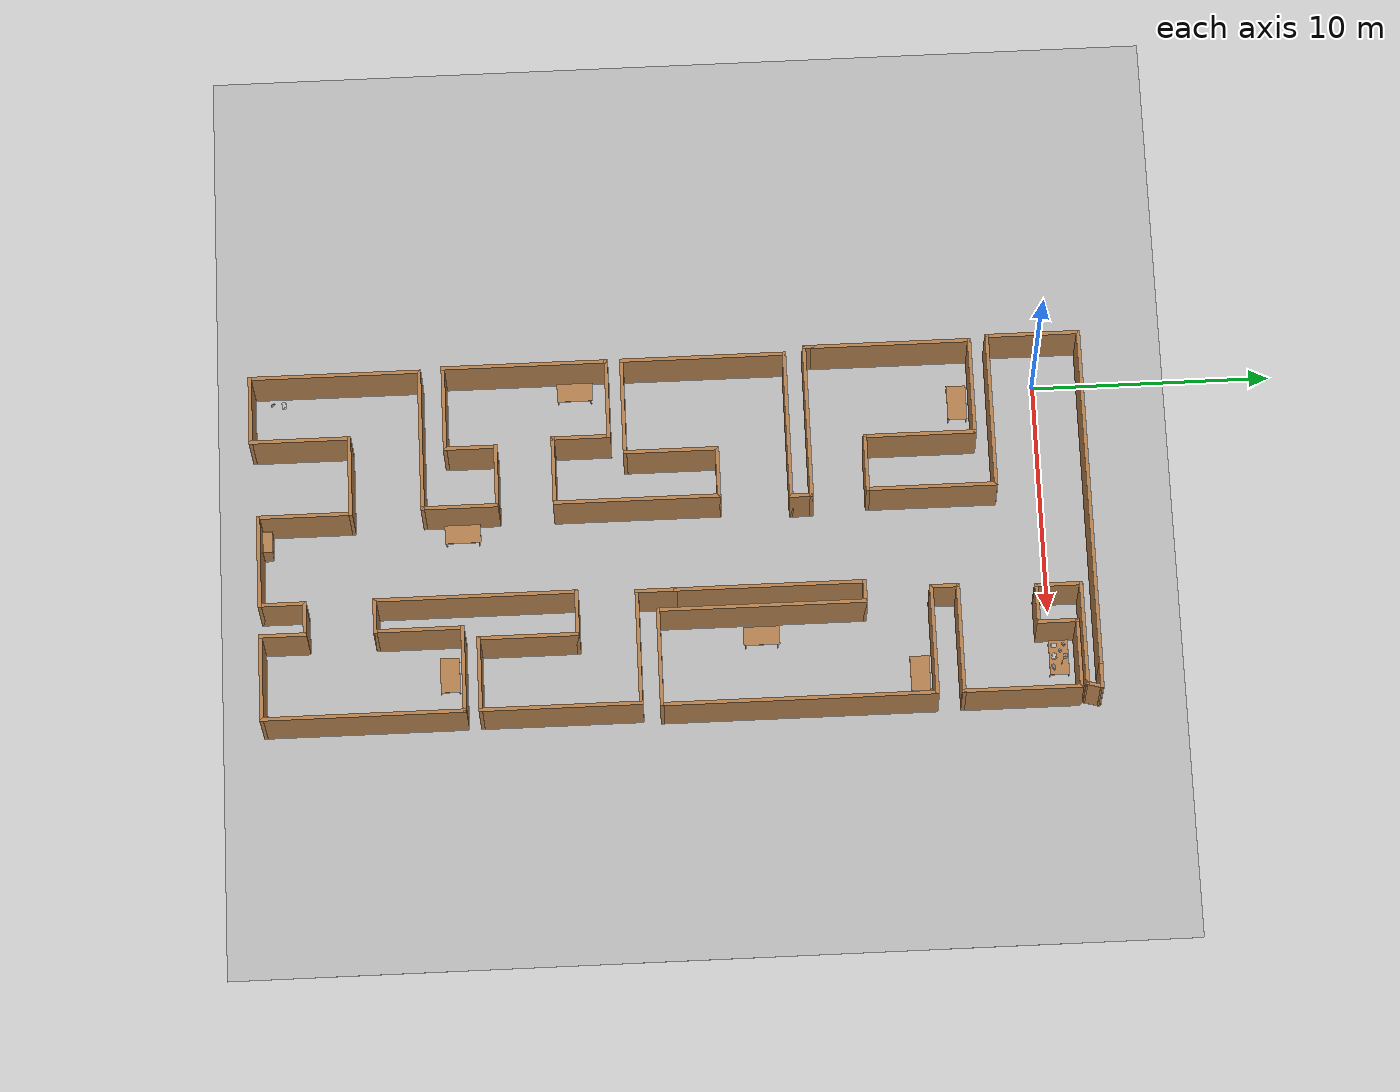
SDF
<sdf version="1.6">
 <world name="default">
  <light name="sun" type="directional">
   <pose>0 0 10 0 -0 0</pose>
   <diffuse>0.8 0.8 0.8 1</diffuse>
   <specular>0.2 0.2 0.2 1</specular>
   <attenuation>
    <range>1000</range>
    <constant>0.9</constant>
    <linear>0.01</linear>
    <quadratic>0.001</quadratic>
   </attenuation>
   <direction>-0.5 0.1 -0.9</direction>
  </light>
  <model name="ground_plane">
   <static>1</static>
   <link name="link">
    <collision name="collision">
     <geometry><plane><normal>0 0 1</normal><size>100 100</size></plane></geometry>
     <surface>
      <contact><collide_bitmask>65535</collide_bitmask></contact>
      <friction><ode><mu>100</mu><mu2>50</mu2></ode></friction>
     </surface>
    </collision>
    <visual name="visual">
     <cast_shadows>0</cast_shadows>
     <geometry><plane><normal>0 0 1</normal><size>100 100</size></plane></geometry>
     <material>
      <script><uri>file://media/materials/scripts/gazebo.material</uri><name>Gazebo/Grey</name></script>
     </material>
    </visual>
   </link>
  </model>
  <gravity>0 0 -9.8</gravity>
  <magnetic_field>6e-06 2.3e-05 -4.2e-05</magnetic_field>
  <atmosphere type="adiabatic"/>
  <physics name="default_physics" default="0" type="ode">
   <max_step_size>0.001</max_step_size>
   <real_time_factor>1</real_time_factor>
   <real_time_update_rate>1000</real_time_update_rate>
  </physics>
  <scene><ambient>0.4 0.4 0.4 1</ambient><background>0.7 0.7 0.7 1</background><shadows>1</shadows></scene>
  <audio><device>default</device></audio>
  <spherical_coordinates>
   <surface_model>EARTH_WGS84</surface_model>
   <latitude_deg>0</latitude_deg>
   <longitude_deg>0</longitude_deg>
   <elevation>0</elevation>
   <heading_deg>0</heading_deg>
  </spherical_coordinates>
  <model name="eight_comodos">
   <pose>6.30597 -15.5274 0 0 -0 -1.57142</pose>
   <link name="Wall_1">
    <collision name="Wall_1_Collision">
     <geometry><box><size>14.75 0.15 2.5</size></box></geometry>
     <pose>0 0 1.25 0 -0 0</pose>
    </collision>
    <visual name="Wall_1_Visual">
     <pose>0 0 1.25 0 -0 0</pose>
     <geometry><box><size>14.75 0.15 2.5</size></box></geometry>
     <material>
      <script><uri>file://media/materials/scripts/gazebo.material</uri><name>Gazebo/Wood</name></script>
      <ambient>1 1 1 1</ambient>
     </material>
     <meta><layer>0</layer></meta>
    </visual>
    <pose>-17.4243 -0.536073 0 0 -0 -1.5708</pose>
   </link>
   <link name="Wall_10">
    <collision name="Wall_10_Collision">
     <geometry><box><size>0.5 0.15 2.5</size></box></geometry>
     <pose>0 0 1.25 0 -0 0</pose>
    </collision>
    <visual name="Wall_10_Visual">
     <pose>0 0 1.25 0 -0 0</pose>
     <geometry><box><size>0.5 0.15 2.5</size></box></geometry>
     <material>
      <script><uri>file://media/materials/scripts/gazebo.material</uri><name>Gazebo/Wood</name></script>
      <ambient>1 1 1 1</ambient>
     </material>
     <meta><layer>0</layer></meta>
    </visual>
    <pose>-6.04928 -7.68607 0 0 -0 0</pose>
   </link>
   <link name="Wall_11">
    <collision name="Wall_11_Collision">
     <geometry><box><size>6.75 0.15 2.5</size></box></geometry>
     <pose>0 0 1.25 0 -0 0</pose>
    </collision>
    <visual name="Wall_11_Visual">
     <pose>0 0 1.25 0 -0 0</pose>
     <geometry><box><size>6.75 0.15 2.5</size></box></geometry>
     <material>
      <script><uri>file://media/materials/scripts/gazebo.material</uri><name>Gazebo/Wood</name></script>
      <ambient>1 1 1 1</ambient>
     </material>
     <meta><layer>0</layer></meta>
    </visual>
    <pose>-5.87428 -4.38607 0 0 -0 1.5708</pose>
   </link>
   <link name="Wall_12">
    <collision name="Wall_12_Collision">
     <geometry><box><size>1 0.15 2.5</size></box></geometry>
     <pose>0 0 1.25 0 -0 0</pose>
    </collision>
    <visual name="Wall_12_Visual">
     <pose>0 0 1.25 0 -0 0</pose>
     <geometry><box><size>1 0.15 2.5</size></box></geometry>
     <material>
      <script><uri>file://media/materials/scripts/gazebo.material</uri><name>Gazebo/Wood</name></script>
      <ambient>1 1 1 1</ambient>
     </material>
     <meta><layer>0</layer></meta>
    </visual>
    <pose>-5.44928 -1.08607 0 0 -0 0</pose>
   </link>
   <link name="Wall_13">
    <collision name="Wall_13_Collision">
     <geometry><box><size>6.5 0.15 2.5</size></box></geometry>
     <pose>0 0 1.25 0 -0 0</pose>
    </collision>
    <visual name="Wall_13_Visual">
     <pose>0 0 1.25 0 -0 0</pose>
     <geometry><box><size>6.5 0.15 2.5</size></box></geometry>
     <material>
      <script><uri>file://media/materials/scripts/gazebo.material</uri><name>Gazebo/Wood</name></script>
      <ambient>1 1 1 1</ambient>
     </material>
     <meta><layer>0</layer></meta>
    </visual>
    <pose>-5.02428 -4.26107 0 0 -0 -1.5708</pose>
   </link>
   <link name="Wall_14">
    <collision name="Wall_14_Collision">
     <geometry><box><size>7 0.15 2.5</size></box></geometry>
     <pose>0 0 1.25 0 -0 0</pose>
    </collision>
    <visual name="Wall_14_Visual">
     <pose>0 0 1.25 0 -0 0</pose>
     <geometry><box><size>7 0.15 2.5</size></box></geometry>
     <material>
      <script><uri>file://media/materials/scripts/gazebo.material</uri><name>Gazebo/Wood</name></script>
      <ambient>1 1 1 1</ambient>
     </material>
     <meta><layer>0</layer></meta>
    </visual>
    <pose>-1.59928 -7.43607 0 0 -0 0</pose>
   </link>
   <link name="Wall_15">
    <collision name="Wall_15_Collision">
     <geometry><box><size>4.25 0.15 2.5</size></box></geometry>
     <pose>0 0 1.25 0 -0 0</pose>
    </collision>
    <visual name="Wall_15_Visual">
     <pose>0 0 1.25 0 -0 0</pose>
     <geometry><box><size>4.25 0.15 2.5</size></box></geometry>
     <material>
      <script><uri>file://media/materials/scripts/gazebo.material</uri><name>Gazebo/Wood</name></script>
      <ambient>1 1 1 1</ambient>
     </material>
     <meta><layer>0</layer></meta>
    </visual>
    <pose>1.82572 -5.38607 0 0 -0 1.5708</pose>
   </link>
   <link name="Wall_16">
    <collision name="Wall_16_Collision">
     <geometry><box><size>4 0.15 2.5</size></box></geometry>
     <pose>0 0 1.25 0 -0 0</pose>
    </collision>
    <visual name="Wall_16_Visual">
     <pose>0 0 1.25 0 -0 0</pose>
     <geometry><box><size>4 0.15 2.5</size></box></geometry>
     <material>
      <script><uri>file://media/materials/scripts/gazebo.material</uri><name>Gazebo/Wood</name></script>
      <ambient>1 1 1 1</ambient>
     </material>
     <meta><layer>0</layer></meta>
    </visual>
    <pose>-0.09928 -3.33607 0 0 -0 3.14159</pose>
   </link>
   <link name="Wall_17">
    <collision name="Wall_17_Collision">
     <geometry><box><size>2.25 0.15 2.5</size></box></geometry>
     <pose>0 0 1.25 0 -0 0</pose>
    </collision>
    <visual name="Wall_17_Visual">
     <pose>0 0 1.25 0 -0 0</pose>
     <geometry><box><size>2.25 0.15 2.5</size></box></geometry>
     <material>
      <script><uri>file://media/materials/scripts/gazebo.material</uri><name>Gazebo/Wood</name></script>
      <ambient>1 1 1 1</ambient>
     </material>
     <meta><layer>0</layer></meta>
    </visual>
    <pose>-2.02428 -2.28607 0 0 -0 1.5708</pose>
   </link>
   <link name="Wall_18">
    <collision name="Wall_18_Collision">
     <geometry><box><size>7 0.15 2.5</size></box></geometry>
     <pose>0 0 1.25 0 -0 0</pose>
    </collision>
    <visual name="Wall_18_Visual">
     <pose>0 0 1.25 0 -0 0</pose>
     <geometry><box><size>7 0.15 2.5</size></box></geometry>
     <material>
      <script><uri>file://media/materials/scripts/gazebo.material</uri><name>Gazebo/Wood</name></script>
      <ambient>1 1 1 1</ambient>
     </material>
     <meta><layer>0</layer></meta>
    </visual>
    <pose>1.40072 -1.23607 0 0 -0 0</pose>
   </link>
   <link name="Wall_19">
    <collision name="Wall_19_Collision">
     <geometry><box><size>3 0.15 2.5</size></box></geometry>
     <pose>0 0 1.25 0 -0 0</pose>
    </collision>
    <visual name="Wall_19_Visual">
     <pose>0 0 1.25 0 -0 0</pose>
     <geometry><box><size>3 0.15 2.5</size></box></geometry>
     <material>
      <script><uri>file://media/materials/scripts/gazebo.material</uri><name>Gazebo/Wood</name></script>
      <ambient>1 1 1 1</ambient>
     </material>
     <meta><layer>0</layer></meta>
    </visual>
    <pose>4.82572 -2.66107 0 0 -0 -1.5708</pose>
   </link>
   <link name="Wall_2">
    <collision name="Wall_2_Collision">
     <geometry><box><size>4 0.15 2.5</size></box></geometry>
     <pose>0 0 1.25 0 -0 0</pose>
    </collision>
    <visual name="Wall_2_Visual">
     <pose>0 0 1.25 0 -0 0</pose>
     <geometry><box><size>4 0.15 2.5</size></box></geometry>
     <material>
      <script><uri>file://media/materials/scripts/gazebo.material</uri><name>Gazebo/Wood</name></script>
      <ambient>1 1 1 1</ambient>
     </material>
     <meta><layer>0</layer></meta>
    </visual>
    <pose>-15.4993 -7.83607 0 0 -0 0</pose>
   </link>
   <link name="Wall_20">
    <collision name="Wall_20_Collision">
     <geometry><box><size>2.5 0.15 2.5</size></box></geometry>
     <pose>0 0 1.25 0 -0 0</pose>
    </collision>
    <visual name="Wall_20_Visual">
     <pose>0 0 1.25 0 -0 0</pose>
     <geometry><box><size>2.5 0.15 2.5</size></box></geometry>
     <material>
      <script><uri>file://media/materials/scripts/gazebo.material</uri><name>Gazebo/Wood</name></script>
      <ambient>1 1 1 1</ambient>
     </material>
     <meta><layer>0</layer></meta>
    </visual>
    <pose>3.65072 -4.08607 0 0 -0 3.14159</pose>
   </link>
   <link name="Wall_21">
    <collision name="Wall_21_Collision">
     <geometry><box><size>3.5 0.15 2.5</size></box></geometry>
     <pose>0 0 1.25 0 -0 0</pose>
    </collision>
    <visual name="Wall_21_Visual">
     <pose>0 0 1.25 0 -0 0</pose>
     <geometry><box><size>3.5 0.15 2.5</size></box></geometry>
     <material>
      <script><uri>file://media/materials/scripts/gazebo.material</uri><name>Gazebo/Wood</name></script>
      <ambient>1 1 1 1</ambient>
     </material>
     <meta><layer>0</layer></meta>
    </visual>
    <pose>2.47572 -5.76107 0 0 -0 -1.5708</pose>
   </link>
   <link name="Wall_22">
    <collision name="Wall_22_Collision">
     <geometry><box><size>7 0.15 2.5</size></box></geometry>
     <pose>0 0 1.25 0 -0 0</pose>
    </collision>
    <visual name="Wall_22_Visual">
     <pose>0 0 1.25 0 -0 0</pose>
     <geometry><box><size>7 0.15 2.5</size></box></geometry>
     <material>
      <script><uri>file://media/materials/scripts/gazebo.material</uri><name>Gazebo/Wood</name></script>
      <ambient>1 1 1 1</ambient>
     </material>
     <meta><layer>0</layer></meta>
    </visual>
    <pose>5.90072 -7.43607 0 0 -0 0</pose>
   </link>
   <link name="Wall_23">
    <collision name="Wall_23_Collision">
     <geometry><box><size>3.75 0.15 2.5</size></box></geometry>
     <pose>0 0 1.25 0 -0 0</pose>
    </collision>
    <visual name="Wall_23_Visual">
     <pose>0 0 1.25 0 -0 0</pose>
     <geometry><box><size>3.75 0.15 2.5</size></box></geometry>
     <material>
      <script><uri>file://media/materials/scripts/gazebo.material</uri><name>Gazebo/Wood</name></script>
      <ambient>1 1 1 1</ambient>
     </material>
     <meta><layer>0</layer></meta>
    </visual>
    <pose>9.32572 -5.63607 0 0 -0 1.5708</pose>
   </link>
   <link name="Wall_24">
    <collision name="Wall_24_Collision">
     <geometry><box><size>2.25 0.15 2.5</size></box></geometry>
     <pose>0 0 1.25 0 -0 0</pose>
    </collision>
    <visual name="Wall_24_Visual">
     <pose>0 0 1.25 0 -0 0</pose>
     <geometry><box><size>2.25 0.15 2.5</size></box></geometry>
     <material>
      <script><uri>file://media/materials/scripts/gazebo.material</uri><name>Gazebo/Wood</name></script>
      <ambient>1 1 1 1</ambient>
     </material>
     <meta><layer>0</layer></meta>
    </visual>
    <pose>8.27572 -3.83607 0 0 -0 3.14159</pose>
   </link>
   <link name="Wall_25">
    <collision name="Wall_25_Collision">
     <geometry><box><size>2.75 0.15 2.5</size></box></geometry>
     <pose>0 0 1.25 0 -0 0</pose>
    </collision>
    <visual name="Wall_25_Visual">
     <pose>0 0 1.25 0 -0 0</pose>
     <geometry><box><size>2.75 0.15 2.5</size></box></geometry>
     <material>
      <script><uri>file://media/materials/scripts/gazebo.material</uri><name>Gazebo/Wood</name></script>
      <ambient>1 1 1 1</ambient>
     </material>
     <meta><layer>0</layer></meta>
    </visual>
    <pose>7.22572 -2.53607 0 0 -0 1.5708</pose>
   </link>
   <link name="Wall_26">
    <collision name="Wall_26_Collision">
     <geometry><box><size>3.25 0.15 2.5</size></box></geometry>
     <pose>0 0 1.25 0 -0 0</pose>
    </collision>
    <visual name="Wall_26_Visual">
     <pose>0 0 1.25 0 -0 0</pose>
     <geometry><box><size>3.25 0.15 2.5</size></box></geometry>
     <material>
      <script><uri>file://media/materials/scripts/gazebo.material</uri><name>Gazebo/Wood</name></script>
      <ambient>1 1 1 1</ambient>
     </material>
     <meta><layer>0</layer></meta>
    </visual>
    <pose>8.77572 -1.23607 0 0 -0 0</pose>
   </link>
   <link name="Wall_27">
    <collision name="Wall_27_Collision">
     <geometry><box><size>6.25 0.15 2.5</size></box></geometry>
     <pose>0 0 1.25 0 -0 0</pose>
    </collision>
    <visual name="Wall_27_Visual">
     <pose>0 0 1.25 0 -0 0</pose>
     <geometry><box><size>6.25 0.15 2.5</size></box></geometry>
     <material>
      <script><uri>file://media/materials/scripts/gazebo.material</uri><name>Gazebo/Wood</name></script>
      <ambient>1 1 1 1</ambient>
     </material>
     <meta><layer>0</layer></meta>
    </visual>
    <pose>10.3257 -4.28607 0 0 -0 -1.5708</pose>
   </link>
   <link name="Wall_28">
    <collision name="Wall_28_Collision">
     <geometry><box><size>7.25 0.15 2.5</size></box></geometry>
     <pose>0 0 1.25 0 -0 0</pose>
    </collision>
    <visual name="Wall_28_Visual">
     <pose>0 0 1.25 0 -0 0</pose>
     <geometry><box><size>7.25 0.15 2.5</size></box></geometry>
     <material>
      <script><uri>file://media/materials/scripts/gazebo.material</uri><name>Gazebo/Wood</name></script>
      <ambient>1 1 1 1</ambient>
     </material>
     <meta><layer>0</layer></meta>
    </visual>
    <pose>13.8757 -7.33607 0 0 -0 0</pose>
   </link>
   <link name="Wall_29">
    <collision name="Wall_29_Collision">
     <geometry><box><size>3 0.15 2.5</size></box></geometry>
     <pose>0 0 1.25 0 -0 0</pose>
    </collision>
    <visual name="Wall_29_Visual">
     <pose>0 0 1.25 0 -0 0</pose>
     <geometry><box><size>3 0.15 2.5</size></box></geometry>
     <material>
      <script><uri>file://media/materials/scripts/gazebo.material</uri><name>Gazebo/Wood</name></script>
      <ambient>1 1 1 1</ambient>
     </material>
     <meta><layer>0</layer></meta>
    </visual>
    <pose>17.4257 -5.91107 0 0 -0 1.5708</pose>
   </link>
   <link name="Wall_3">
    <collision name="Wall_3_Collision">
     <geometry><box><size>6.75 0.15 2.5</size></box></geometry>
     <pose>0 0 1.25 0 -0 0</pose>
    </collision>
    <visual name="Wall_3_Visual">
     <pose>0 0 1.25 0 -0 0</pose>
     <geometry><box><size>6.75 0.15 2.5</size></box></geometry>
     <material>
      <script><uri>file://media/materials/scripts/gazebo.material</uri><name>Gazebo/Wood</name></script>
      <ambient>1 1 1 1</ambient>
     </material>
     <meta><layer>0</layer></meta>
    </visual>
    <pose>-13.5743 -4.53607 0 0 -0 1.5708</pose>
   </link>
   <link name="Wall_30">
    <collision name="Wall_30_Collision">
     <geometry><box><size>4.25 0.15 2.5</size></box></geometry>
     <pose>0 0 1.25 0 -0 0</pose>
    </collision>
    <visual name="Wall_30_Visual">
     <pose>0 0 1.25 0 -0 0</pose>
     <geometry><box><size>4.25 0.15 2.5</size></box></geometry>
     <material>
      <script><uri>file://media/materials/scripts/gazebo.material</uri><name>Gazebo/Wood</name></script>
      <ambient>1 1 1 1</ambient>
     </material>
     <meta><layer>0</layer></meta>
    </visual>
    <pose>15.3757 -4.48607 0 0 -0 3.14159</pose>
   </link>
   <link name="Wall_31">
    <collision name="Wall_31_Collision">
     <geometry><box><size>3.5 0.15 2.5</size></box></geometry>
     <pose>0 0 1.25 0 -0 0</pose>
    </collision>
    <visual name="Wall_31_Visual">
     <pose>0 0 1.25 0 -0 0</pose>
     <geometry><box><size>3.5 0.15 2.5</size></box></geometry>
     <material>
      <script><uri>file://media/materials/scripts/gazebo.material</uri><name>Gazebo/Wood</name></script>
      <ambient>1 1 1 1</ambient>
     </material>
     <meta><layer>0</layer></meta>
    </visual>
    <pose>13.3257 -2.81107 0 0 -0 1.5708</pose>
   </link>
   <link name="Wall_32">
    <collision name="Wall_32_Collision">
     <geometry><box><size>4 0.15 2.5</size></box></geometry>
     <pose>0 0 1.25 0 -0 0</pose>
    </collision>
    <visual name="Wall_32_Visual">
     <pose>0 0 1.25 0 -0 0</pose>
     <geometry><box><size>4 0.15 2.5</size></box></geometry>
     <material>
      <script><uri>file://media/materials/scripts/gazebo.material</uri><name>Gazebo/Wood</name></script>
      <ambient>1 1 1 1</ambient>
     </material>
     <meta><layer>0</layer></meta>
    </visual>
    <pose>15.2507 -1.13607 0 0 -0 0</pose>
   </link>
   <link name="Wall_33">
    <collision name="Wall_33_Collision">
     <geometry><box><size>4 0.15 2.5</size></box></geometry>
     <pose>0 0 1.25 0 -0 0</pose>
    </collision>
    <visual name="Wall_33_Visual">
     <pose>0 0 1.25 0 -0 0</pose>
     <geometry><box><size>4 0.15 2.5</size></box></geometry>
     <material>
      <script><uri>file://media/materials/scripts/gazebo.material</uri><name>Gazebo/Wood</name></script>
      <ambient>1 1 1 1</ambient>
     </material>
     <meta><layer>0</layer></meta>
    </visual>
    <pose>17.1757 0.788927 0 0 -0 1.5708</pose>
   </link>
   <link name="Wall_34">
    <collision name="Wall_34_Collision">
     <geometry><box><size>2 0.15 2.5</size></box></geometry>
     <pose>0 0 1.25 0 -0 0</pose>
    </collision>
    <visual name="Wall_34_Visual">
     <pose>0 0 1.25 0 -0 0</pose>
     <geometry><box><size>2 0.15 2.5</size></box></geometry>
     <material>
      <script><uri>file://media/materials/scripts/gazebo.material</uri><name>Gazebo/Wood</name></script>
      <ambient>1 1 1 1</ambient>
     </material>
     <meta><layer>0</layer></meta>
    </visual>
    <pose>16.2507 2.71393 0 0 -0 3.14159</pose>
   </link>
   <link name="Wall_35">
    <collision name="Wall_35_Collision">
     <geometry><box><size>1.5 0.15 2.5</size></box></geometry>
     <pose>0 0 1.25 0 -0 0</pose>
    </collision>
    <visual name="Wall_35_Visual">
     <pose>0 0 1.25 0 -0 0</pose>
     <geometry><box><size>1.5 0.15 2.5</size></box></geometry>
     <material>
      <script><uri>file://media/materials/scripts/gazebo.material</uri><name>Gazebo/Wood</name></script>
      <ambient>1 1 1 1</ambient>
     </material>
     <meta><layer>0</layer></meta>
    </visual>
    <pose>15.3257 3.38893 0 0 -0 1.5708</pose>
   </link>
   <link name="Wall_36">
    <collision name="Wall_36_Collision">
     <geometry><box><size>2 0.15 2.5</size></box></geometry>
     <pose>0 0 1.25 0 -0 0</pose>
    </collision>
    <visual name="Wall_36_Visual">
     <pose>0 0 1.25 0 -0 0</pose>
     <geometry><box><size>2 0.15 2.5</size></box></geometry>
     <material>
      <script><uri>file://media/materials/scripts/gazebo.material</uri><name>Gazebo/Wood</name></script>
      <ambient>1 1 1 1</ambient>
     </material>
     <meta><layer>0</layer></meta>
    </visual>
    <pose>16.2507 4.06393 0 0 -0 0</pose>
   </link>
   <link name="Wall_37">
    <collision name="Wall_37_Collision">
     <geometry><box><size>3.75 0.15 2.5</size></box></geometry>
     <pose>0 0 1.25 0 -0 0</pose>
    </collision>
    <visual name="Wall_37_Visual">
     <pose>0 0 1.25 0 -0 0</pose>
     <geometry><box><size>3.75 0.15 2.5</size></box></geometry>
     <material>
      <script><uri>file://media/materials/scripts/gazebo.material</uri><name>Gazebo/Wood</name></script>
      <ambient>1 1 1 1</ambient>
     </material>
     <meta><layer>0</layer></meta>
    </visual>
    <pose>17.1757 5.86393 0 0 -0 1.5708</pose>
   </link>
   <link name="Wall_38">
    <collision name="Wall_38_Collision">
     <geometry><box><size>8.5 0.15 2.5</size></box></geometry>
     <pose>0 0 1.25 0 -0 0</pose>
    </collision>
    <visual name="Wall_38_Visual">
     <pose>0 0 1.25 0 -0 0</pose>
     <geometry><box><size>8.5 0.15 2.5</size></box></geometry>
     <material>
      <script><uri>file://media/materials/scripts/gazebo.material</uri><name>Gazebo/Wood</name></script>
      <ambient>1 1 1 1</ambient>
     </material>
     <meta><layer>0</layer></meta>
    </visual>
    <pose>13.0007 7.66393 0 0 -0 3.14159</pose>
   </link>
   <link name="Wall_39">
    <collision name="Wall_39_Collision">
     <geometry><box><size>3.75 0.15 2.5</size></box></geometry>
     <pose>0 0 1.25 0 -0 0</pose>
    </collision>
    <visual name="Wall_39_Visual">
     <pose>0 0 1.25 0 -0 0</pose>
     <geometry><box><size>3.75 0.15 2.5</size></box></geometry>
     <material>
      <script><uri>file://media/materials/scripts/gazebo.material</uri><name>Gazebo/Wood</name></script>
      <ambient>1 1 1 1</ambient>
     </material>
     <meta><layer>0</layer></meta>
    </visual>
    <pose>8.82572 5.86393 0 0 -0 -1.5708</pose>
   </link>
   <link name="Wall_4">
    <collision name="Wall_4_Collision">
     <geometry><box><size>5.5 0.15 2.5</size></box></geometry>
     <pose>0 0 1.25 0 -0 0</pose>
    </collision>
    <visual name="Wall_4_Visual">
     <pose>0 0 1.25 0 -0 0</pose>
     <geometry><box><size>5.5 0.15 2.5</size></box></geometry>
     <material>
      <script><uri>file://media/materials/scripts/gazebo.material</uri><name>Gazebo/Wood</name></script>
      <ambient>1 1 1 1</ambient>
     </material>
     <meta><layer>0</layer></meta>
    </visual>
    <pose>-10.8993 -1.23607 0 0 -0 0</pose>
   </link>
   <link name="Wall_40">
    <collision name="Wall_40_Collision">
     <geometry><box><size>3.75 0.15 2.5</size></box></geometry>
     <pose>0 0 1.25 0 -0 0</pose>
    </collision>
    <visual name="Wall_40_Visual">
     <pose>0 0 1.25 0 -0 0</pose>
     <geometry><box><size>3.75 0.15 2.5</size></box></geometry>
     <material>
      <script><uri>file://media/materials/scripts/gazebo.material</uri><name>Gazebo/Wood</name></script>
      <ambient>1 1 1 1</ambient>
     </material>
     <meta><layer>0</layer></meta>
    </visual>
    <pose>10.6257 4.06393 0 0 -0 0</pose>
   </link>
   <link name="Wall_41">
    <collision name="Wall_41_Collision">
     <geometry><box><size>1.5 0.15 2.5</size></box></geometry>
     <pose>0 0 1.25 0 -0 0</pose>
    </collision>
    <visual name="Wall_41_Visual">
     <pose>0 0 1.25 0 -0 0</pose>
     <geometry><box><size>1.5 0.15 2.5</size></box></geometry>
     <material>
      <script><uri>file://media/materials/scripts/gazebo.material</uri><name>Gazebo/Wood</name></script>
      <ambient>1 1 1 1</ambient>
     </material>
     <meta><layer>0</layer></meta>
    </visual>
    <pose>12.4257 3.38893 0 0 -0 -1.5708</pose>
   </link>
   <link name="Wall_42">
    <collision name="Wall_42_Collision">
     <geometry><box><size>8.5 0.15 2.5</size></box></geometry>
     <pose>0 0 1.25 0 -0 0</pose>
    </collision>
    <visual name="Wall_42_Visual">
     <pose>0 0 1.25 0 -0 0</pose>
     <geometry><box><size>8.5 0.15 2.5</size></box></geometry>
     <material>
      <script><uri>file://media/materials/scripts/gazebo.material</uri><name>Gazebo/Wood</name></script>
      <ambient>1 1 1 1</ambient>
     </material>
     <meta><layer>0</layer></meta>
    </visual>
    <pose>8.25072 2.71393 0 0 -0 3.14159</pose>
   </link>
   <link name="Wall_43">
    <collision name="Wall_43_Collision">
     <geometry><box><size>2 0.15 2.5</size></box></geometry>
     <pose>0 0 1.25 0 -0 0</pose>
    </collision>
    <visual name="Wall_43_Visual">
     <pose>0 0 1.25 0 -0 0</pose>
     <geometry><box><size>2 0.15 2.5</size></box></geometry>
     <material>
      <script><uri>file://media/materials/scripts/gazebo.material</uri><name>Gazebo/Wood</name></script>
      <ambient>1 1 1 1</ambient>
     </material>
     <meta><layer>0</layer></meta>
    </visual>
    <pose>4.07572 3.63893 0 0 -0 1.5708</pose>
   </link>
   <link name="Wall_44">
    <collision name="Wall_44_Collision">
     <geometry><box><size>4.25 0.15 2.5</size></box></geometry>
     <pose>0 0 1.25 0 -0 0</pose>
    </collision>
    <visual name="Wall_44_Visual">
     <pose>0 0 1.25 0 -0 0</pose>
     <geometry><box><size>4.25 0.15 2.5</size></box></geometry>
     <material>
      <script><uri>file://media/materials/scripts/gazebo.material</uri><name>Gazebo/Wood</name></script>
      <ambient>1 1 1 1</ambient>
     </material>
     <meta><layer>0</layer></meta>
    </visual>
    <pose>6.12572 4.56393 0 0 -0 0</pose>
   </link>
   <link name="Wall_45">
    <collision name="Wall_45_Collision">
     <geometry><box><size>3.25 0.15 2.5</size></box></geometry>
     <pose>0 0 1.25 0 -0 0</pose>
    </collision>
    <visual name="Wall_45_Visual">
     <pose>0 0 1.25 0 -0 0</pose>
     <geometry><box><size>3.25 0.15 2.5</size></box></geometry>
     <material>
      <script><uri>file://media/materials/scripts/gazebo.material</uri><name>Gazebo/Wood</name></script>
      <ambient>1 1 1 1</ambient>
     </material>
     <meta><layer>0</layer></meta>
    </visual>
    <pose>8.17572 6.11393 0 0 -0 1.5708</pose>
   </link>
   <link name="Wall_46">
    <collision name="Wall_46_Collision">
     <geometry><box><size>6.75 0.15 2.5</size></box></geometry>
     <pose>0 0 1.25 0 -0 0</pose>
    </collision>
    <visual name="Wall_46_Visual">
     <pose>0 0 1.25 0 -0 0</pose>
     <geometry><box><size>6.75 0.15 2.5</size></box></geometry>
     <material>
      <script><uri>file://media/materials/scripts/gazebo.material</uri><name>Gazebo/Wood</name></script>
      <ambient>1 1 1 1</ambient>
     </material>
     <meta><layer>0</layer></meta>
    </visual>
    <pose>4.87572 7.66393 0 0 -0 3.14159</pose>
   </link>
   <link name="Wall_47">
    <collision name="Wall_47_Collision">
     <geometry><box><size>5 0.15 2.5</size></box></geometry>
     <pose>0 0 1.25 0 -0 0</pose>
    </collision>
    <visual name="Wall_47_Visual">
     <pose>0 0 1.25 0 -0 0</pose>
     <geometry><box><size>5 0.15 2.5</size></box></geometry>
     <material>
      <script><uri>file://media/materials/scripts/gazebo.material</uri><name>Gazebo/Wood</name></script>
      <ambient>1 1 1 1</ambient>
     </material>
     <meta><layer>0</layer></meta>
    </visual>
    <pose>1.57572 5.23893 0 0 -0 -1.5708</pose>
   </link>
   <link name="Wall_48">
    <collision name="Wall_48_Collision">
     <geometry><box><size>1.75 0.15 2.5</size></box></geometry>
     <pose>0 0 1.25 0 -0 0</pose>
    </collision>
    <visual name="Wall_48_Visual">
     <pose>0 0 1.25 0 -0 0</pose>
     <geometry><box><size>1.75 0.15 2.5</size></box></geometry>
     <material>
      <script><uri>file://media/materials/scripts/gazebo.material</uri><name>Gazebo/Wood</name></script>
      <ambient>1 1 1 1</ambient>
     </material>
     <meta><layer>0</layer></meta>
    </visual>
    <pose>0.775719 2.81393 0 0 -0 3.14159</pose>
   </link>
   <link name="Wall_49">
    <collision name="Wall_49_Collision">
     <geometry><box><size>8 0.15 2.5</size></box></geometry>
     <pose>0 0 1.25 0 -0 0</pose>
    </collision>
    <visual name="Wall_49_Visual">
     <pose>0 0 1.25 0 -0 0</pose>
     <geometry><box><size>8 0.15 2.5</size></box></geometry>
     <material>
      <script><uri>file://media/materials/scripts/gazebo.material</uri><name>Gazebo/Wood</name></script>
      <ambient>1 1 1 1</ambient>
     </material>
     <meta><layer>0</layer></meta>
    </visual>
    <pose>-3.94928 2.81393 0 0 -0 3.14159</pose>
   </link>
   <link name="Wall_5">
    <collision name="Wall_5_Collision">
     <geometry><box><size>2.5 0.15 2.5</size></box></geometry>
     <pose>0 0 1.25 0 -0 0</pose>
    </collision>
    <visual name="Wall_5_Visual">
     <pose>0 0 1.25 0 -0 0</pose>
     <geometry><box><size>2.5 0.15 2.5</size></box></geometry>
     <material>
      <script><uri>file://media/materials/scripts/gazebo.material</uri><name>Gazebo/Wood</name></script>
      <ambient>1 1 1 1</ambient>
     </material>
     <meta><layer>0</layer></meta>
    </visual>
    <pose>-8.22428 -2.41107 0 0 -0 -1.5708</pose>
   </link>
   <link name="Wall_50">
    <collision name="Wall_50_Collision">
     <geometry><box><size>1 0.15 2.5</size></box></geometry>
     <pose>0 0 1.25 0 -0 0</pose>
    </collision>
    <visual name="Wall_50_Visual">
     <pose>0 0 1.25 0 -0 0</pose>
     <geometry><box><size>1 0.15 2.5</size></box></geometry>
     <material>
      <script><uri>file://media/materials/scripts/gazebo.material</uri><name>Gazebo/Wood</name></script>
      <ambient>1 1 1 1</ambient>
     </material>
     <meta><layer>0</layer></meta>
    </visual>
    <pose>-7.87428 3.23893 0 0 -0 1.5708</pose>
   </link>
   <link name="Wall_51">
    <collision name="Wall_51_Collision">
     <geometry><box><size>8.75 0.15 2.5</size></box></geometry>
     <pose>0 0 1.25 0 -0 0</pose>
    </collision>
    <visual name="Wall_51_Visual">
     <pose>0 0 1.25 0 -0 0</pose>
     <geometry><box><size>8.75 0.15 2.5</size></box></geometry>
     <material>
      <script><uri>file://media/materials/scripts/gazebo.material</uri><name>Gazebo/Wood</name></script>
      <ambient>1 1 1 1</ambient>
     </material>
     <meta><layer>0</layer></meta>
    </visual>
    <pose>-3.57428 3.66393 0 0 -0 0</pose>
   </link>
   <link name="Wall_52">
    <collision name="Wall_52_Collision">
     <geometry><box><size>4.25 0.15 2.5</size></box></geometry>
     <pose>0 0 1.25 0 -0 0</pose>
    </collision>
    <visual name="Wall_52_Visual">
     <pose>0 0 1.25 0 -0 0</pose>
     <geometry><box><size>4.25 0.15 2.5</size></box></geometry>
     <material>
      <script><uri>file://media/materials/scripts/gazebo.material</uri><name>Gazebo/Wood</name></script>
      <ambient>1 1 1 1</ambient>
     </material>
     <meta><layer>0</layer></meta>
    </visual>
    <pose>0.725719 5.71393 0 0 -0 1.5708</pose>
   </link>
   <link name="Wall_53">
    <collision name="Wall_53_Collision">
     <geometry><box><size>11.5 0.15 2.5</size></box></geometry>
     <pose>0 0 1.25 0 -0 0</pose>
    </collision>
    <visual name="Wall_53_Visual">
     <pose>0 0 1.25 0 -0 0</pose>
     <geometry><box><size>11.5 0.15 2.5</size></box></geometry>
     <material>
      <script><uri>file://media/materials/scripts/gazebo.material</uri><name>Gazebo/Wood</name></script>
      <ambient>1 1 1 1</ambient>
     </material>
     <meta><layer>0</layer></meta>
    </visual>
    <pose>-4.94928 7.76393 0 0 -0 3.14159</pose>
   </link>
   <link name="Wall_54">
    <collision name="Wall_54_Collision">
     <geometry><box><size>4.75 0.15 2.5</size></box></geometry>
     <pose>0 0 1.25 0 -0 0</pose>
    </collision>
    <visual name="Wall_54_Visual">
     <pose>0 0 1.25 0 -0 0</pose>
     <geometry><box><size>4.75 0.15 2.5</size></box></geometry>
     <material>
      <script><uri>file://media/materials/scripts/gazebo.material</uri><name>Gazebo/Wood</name></script>
      <ambient>1 1 1 1</ambient>
     </material>
     <meta><layer>0</layer></meta>
    </visual>
    <pose>-10.6243 5.46393 0 0 -0 -1.5708</pose>
   </link>
   <link name="Wall_55">
    <collision name="Wall_55_Collision">
     <geometry><box><size>1.25 0.15 2.5</size></box></geometry>
     <pose>0 0 1.25 0 -0 0</pose>
    </collision>
    <visual name="Wall_55_Visual">
     <pose>0 0 1.25 0 -0 0</pose>
     <geometry><box><size>1.25 0.15 2.5</size></box></geometry>
     <material>
      <script><uri>file://media/materials/scripts/gazebo.material</uri><name>Gazebo/Wood</name></script>
      <ambient>1 1 1 1</ambient>
     </material>
     <meta><layer>0</layer></meta>
    </visual>
    <pose>-11.1743 3.16393 0 0 -0 3.14159</pose>
   </link>
   <link name="Wall_56">
    <collision name="Wall_56_Collision">
     <geometry><box><size>4.75 0.15 2.5</size></box></geometry>
     <pose>0 0 1.25 0 -0 0</pose>
    </collision>
    <visual name="Wall_56_Visual">
     <pose>0 0 1.25 0 -0 0</pose>
     <geometry><box><size>4.75 0.15 2.5</size></box></geometry>
     <material>
      <script><uri>file://media/materials/scripts/gazebo.material</uri><name>Gazebo/Wood</name></script>
      <ambient>1 1 1 1</ambient>
     </material>
     <meta><layer>0</layer></meta>
    </visual>
    <pose>-11.7243 5.46393 0 0 -0 1.5708</pose>
   </link>
   <link name="Wall_57">
    <collision name="Wall_57_Collision">
     <geometry><box><size>5 0.15 2.5</size></box></geometry>
     <pose>0 0 1.25 0 -0 0</pose>
    </collision>
    <visual name="Wall_57_Visual">
     <pose>0 0 1.25 0 -0 0</pose>
     <geometry><box><size>5 0.15 2.5</size></box></geometry>
     <material>
      <script><uri>file://media/materials/scripts/gazebo.material</uri><name>Gazebo/Wood</name></script>
      <ambient>1 1 1 1</ambient>
     </material>
     <meta><layer>0</layer></meta>
    </visual>
    <pose>-14.1493 7.76393 0 0 -0 3.14159</pose>
   </link>
   <link name="Wall_58">
    <collision name="Wall_58_Collision">
     <geometry><box><size>3 0.15 2.5</size></box></geometry>
     <pose>0 0 1.25 0 -0 0</pose>
    </collision>
    <visual name="Wall_58_Visual">
     <pose>0 0 1.25 0 -0 0</pose>
     <geometry><box><size>3 0.15 2.5</size></box></geometry>
     <material>
      <script><uri>file://media/materials/scripts/gazebo.material</uri><name>Gazebo/Wood</name></script>
      <ambient>1 1 1 1</ambient>
     </material>
     <meta><layer>0</layer></meta>
    </visual>
    <pose>-16.5743 6.33893 0 0 -0 -1.5708</pose>
   </link>
   <link name="Wall_59">
    <collision name="Wall_59_Collision">
     <geometry><box><size>1.75 0.15 2.5</size></box></geometry>
     <pose>0 0 1.25 0 -0 0</pose>
    </collision>
    <visual name="Wall_59_Visual">
     <pose>0 0 1.25 0 -0 0</pose>
     <geometry><box><size>1.75 0.15 2.5</size></box></geometry>
     <material>
      <script><uri>file://media/materials/scripts/gazebo.material</uri><name>Gazebo/Wood</name></script>
      <ambient>1 1 1 1</ambient>
     </material>
     <meta><layer>0</layer></meta>
    </visual>
    <pose>-15.7743 4.91393 0 0 -0 0</pose>
   </link>
   <link name="Wall_6">
    <collision name="Wall_6_Collision">
     <geometry><box><size>4.75 0.15 2.5</size></box></geometry>
     <pose>0 0 1.25 0 -0 0</pose>
    </collision>
    <visual name="Wall_6_Visual">
     <pose>0 0 1.25 0 -0 0</pose>
     <geometry><box><size>4.75 0.15 2.5</size></box></geometry>
     <material>
      <script><uri>file://media/materials/scripts/gazebo.material</uri><name>Gazebo/Wood</name></script>
      <ambient>1 1 1 1</ambient>
     </material>
     <meta><layer>0</layer></meta>
    </visual>
    <pose>-10.5243 -3.58607 0 0 -0 3.14159</pose>
   </link>
   <link name="Wall_60">
    <collision name="Wall_60_Collision">
     <geometry><box><size>1.75 0.15 2.5</size></box></geometry>
     <pose>0 0 1.25 0 -0 0</pose>
    </collision>
    <visual name="Wall_60_Visual">
     <pose>0 0 1.25 0 -0 0</pose>
     <geometry><box><size>1.75 0.15 2.5</size></box></geometry>
     <material>
      <script><uri>file://media/materials/scripts/gazebo.material</uri><name>Gazebo/Wood</name></script>
      <ambient>1 1 1 1</ambient>
     </material>
     <meta><layer>0</layer></meta>
    </visual>
    <pose>-14.9743 4.11393 0 0 -0 -1.5708</pose>
   </link>
   <link name="Wall_61">
    <collision name="Wall_61_Collision">
     <geometry><box><size>2 0.15 2.5</size></box></geometry>
     <pose>0 0 1.25 0 -0 0</pose>
    </collision>
    <visual name="Wall_61_Visual">
     <pose>0 0 1.25 0 -0 0</pose>
     <geometry><box><size>2 0.15 2.5</size></box></geometry>
     <material>
      <script><uri>file://media/materials/scripts/gazebo.material</uri><name>Gazebo/Wood</name></script>
      <ambient>1 1 1 1</ambient>
     </material>
     <meta><layer>0</layer></meta>
    </visual>
    <pose>-15.8993 3.31393 0 0 -0 3.14159</pose>
   </link>
   <link name="Wall_62">
    <collision name="Wall_62_Collision">
     <geometry><box><size>4.5 0.15 2.5</size></box></geometry>
     <pose>0 0 1.25 0 -0 0</pose>
    </collision>
    <visual name="Wall_62_Visual">
     <pose>0 0 1.25 0 -0 0</pose>
     <geometry><box><size>4.5 0.15 2.5</size></box></geometry>
     <material>
      <script><uri>file://media/materials/scripts/gazebo.material</uri><name>Gazebo/Wood</name></script>
      <ambient>1 1 1 1</ambient>
     </material>
     <meta><layer>0</layer></meta>
    </visual>
    <pose>-16.8243 5.48893 0 0 -0 1.5708</pose>
   </link>
   <link name="Wall_63">
    <collision name="Wall_63_Collision">
     <geometry><box><size>0.75 0.15 2.5</size></box></geometry>
     <pose>0 0 1.25 0 -0 0</pose>
    </collision>
    <visual name="Wall_63_Visual">
     <pose>0 0 1.25 0 -0 0</pose>
     <geometry><box><size>0.75 0.15 2.5</size></box></geometry>
     <material>
      <script><uri>file://media/materials/scripts/gazebo.material</uri><name>Gazebo/Wood</name></script>
      <ambient>1 1 1 1</ambient>
     </material>
     <meta><layer>0</layer></meta>
    </visual>
    <pose>-17.1141 7.74157 0 0 -0 2.87979</pose>
   </link>
   <link name="Wall_64">
    <collision name="Wall_64_Collision">
     <geometry><box><size>1.20549 0.15 2.5</size></box></geometry>
     <pose>0 0 1.25 0 -0 0</pose>
    </collision>
    <visual name="Wall_64_Visual">
     <pose>0 0 1.25 0 -0 0</pose>
     <geometry><box><size>1.20549 0.15 2.5</size></box></geometry>
     <material>
      <script><uri>file://media/materials/scripts/gazebo.material</uri><name>Gazebo/Wood</name></script>
      <ambient>1 1 1 1</ambient>
     </material>
     <meta><layer>0</layer></meta>
    </visual>
    <pose>-17.4141 7.29157 0 0 -0 -1.59017</pose>
   </link>
   <link name="Wall_7">
    <collision name="Wall_7_Collision">
     <geometry><box><size>4.25 0.15 2.5</size></box></geometry>
     <pose>0 0 1.25 0 -0 0</pose>
    </collision>
    <visual name="Wall_7_Visual">
     <pose>0 0 1.25 0 -0 0</pose>
     <geometry><box><size>4.25 0.15 2.5</size></box></geometry>
     <material>
      <script><uri>file://media/materials/scripts/gazebo.material</uri><name>Gazebo/Wood</name></script>
      <ambient>1 1 1 1</ambient>
     </material>
     <meta><layer>0</layer></meta>
    </visual>
    <pose>-12.8243 -5.63607 0 0 -0 -1.5708</pose>
   </link>
   <link name="Wall_8">
    <collision name="Wall_8_Collision">
     <geometry><box><size>6.75 0.15 2.5</size></box></geometry>
     <pose>0 0 1.25 0 -0 0</pose>
    </collision>
    <visual name="Wall_8_Visual">
     <pose>0 0 1.25 0 -0 0</pose>
     <geometry><box><size>6.75 0.15 2.5</size></box></geometry>
     <material>
      <script><uri>file://media/materials/scripts/gazebo.material</uri><name>Gazebo/Wood</name></script>
      <ambient>1 1 1 1</ambient>
     </material>
     <meta><layer>0</layer></meta>
    </visual>
    <pose>-9.52428 -7.68607 0 0 -0 0</pose>
   </link>
   <static>1</static>
  </model>
  <model name="table">
   <static>1</static>
   <link name="link">
    <collision name="surface">
     <pose>0 0 1 0 -0 0</pose>
     <geometry><box><size>1.5 0.8 0.03</size></box></geometry>
     <surface><friction><ode><mu>0.6</mu><mu2>0.6</mu2></ode></friction></surface>
    </collision>
    <visual name="visual1">
     <pose>0 0 1 0 -0 0</pose>
     <geometry><box><size>1.5 0.8 0.03</size></box></geometry>
     <material>
      <script><uri>file://media/materials/scripts/gazebo.material</uri><name>Gazebo/Wood</name></script>
     </material>
    </visual>
    <collision name="front_left_leg">
     <pose>0.68 0.38 0.5 0 -0 0</pose>
     <geometry><cylinder><radius>0.02</radius><length>1</length></cylinder></geometry>
    </collision>
    <visual name="front_left_leg">
     <pose>0.68 0.38 0.5 0 -0 0</pose>
     <geometry><cylinder><radius>0.02</radius><length>1</length></cylinder></geometry>
     <material>
      <script><uri>file://media/materials/scripts/gazebo.material</uri><name>Gazebo/Grey</name></script>
     </material>
    </visual>
    <collision name="front_right_leg">
     <pose>0.68 -0.38 0.5 0 -0 0</pose>
     <geometry><cylinder><radius>0.02</radius><length>1</length></cylinder></geometry>
    </collision>
    <visual name="front_right_leg">
     <pose>0.68 -0.38 0.5 0 -0 0</pose>
     <geometry><cylinder><radius>0.02</radius><length>1</length></cylinder></geometry>
     <material>
      <script><uri>file://media/materials/scripts/gazebo.material</uri><name>Gazebo/Grey</name></script>
     </material>
    </visual>
    <collision name="back_right_leg">
     <pose>-0.68 -0.38 0.5 0 -0 0</pose>
     <geometry><cylinder><radius>0.02</radius><length>1</length></cylinder></geometry>
    </collision>
    <visual name="back_right_leg">
     <pose>-0.68 -0.38 0.5 0 -0 0</pose>
     <geometry><cylinder><radius>0.02</radius><length>1</length></cylinder></geometry>
     <material>
      <script><uri>file://media/materials/scripts/gazebo.material</uri><name>Gazebo/Grey</name></script>
     </material>
    </visual>
    <collision name="back_left_leg">
     <pose>-0.68 0.38 0.5 0 -0 0</pose>
     <geometry><cylinder><radius>0.02</radius><length>1</length></cylinder></geometry>
    </collision>
    <visual name="back_left_leg">
     <pose>-0.68 0.38 0.5 0 -0 0</pose>
     <geometry><cylinder><radius>0.02</radius><length>1</length></cylinder></geometry>
     <material>
      <script><uri>file://media/materials/scripts/gazebo.material</uri><name>Gazebo/Grey</name></script>
     </material>
    </visual>
   </link>
   <pose>12.1604 0.310021 -0.542091 0 -0 0</pose>
  </model>
  <model name="table_0">
   <static>1</static>
   <link name="link">
    <collision name="surface">
     <pose>0 0 1 0 -0 0</pose>
     <geometry><box><size>1.5 0.8 0.03</size></box></geometry>
     <surface><friction><ode><mu>0.6</mu><mu2>0.6</mu2></ode></friction></surface>
    </collision>
    <visual name="visual1">
     <pose>0 0 1 0 -0 0</pose>
     <geometry><box><size>1.5 0.8 0.03</size></box></geometry>
     <material>
      <script><uri>file://media/materials/scripts/gazebo.material</uri><name>Gazebo/Wood</name></script>
     </material>
    </visual>
    <collision name="front_left_leg">
     <pose>0.68 0.38 0.5 0 -0 0</pose>
     <geometry><cylinder><radius>0.02</radius><length>1</length></cylinder></geometry>
    </collision>
    <visual name="front_left_leg">
     <pose>0.68 0.38 0.5 0 -0 0</pose>
     <geometry><cylinder><radius>0.02</radius><length>1</length></cylinder></geometry>
     <material>
      <script><uri>file://media/materials/scripts/gazebo.material</uri><name>Gazebo/Grey</name></script>
     </material>
    </visual>
    <collision name="front_right_leg">
     <pose>0.68 -0.38 0.5 0 -0 0</pose>
     <geometry><cylinder><radius>0.02</radius><length>1</length></cylinder></geometry>
    </collision>
    <visual name="front_right_leg">
     <pose>0.68 -0.38 0.5 0 -0 0</pose>
     <geometry><cylinder><radius>0.02</radius><length>1</length></cylinder></geometry>
     <material>
      <script><uri>file://media/materials/scripts/gazebo.material</uri><name>Gazebo/Grey</name></script>
     </material>
    </visual>
    <collision name="back_right_leg">
     <pose>-0.68 -0.38 0.5 0 -0 0</pose>
     <geometry><cylinder><radius>0.02</radius><length>1</length></cylinder></geometry>
    </collision>
    <visual name="back_right_leg">
     <pose>-0.68 -0.38 0.5 0 -0 0</pose>
     <geometry><cylinder><radius>0.02</radius><length>1</length></cylinder></geometry>
     <material>
      <script><uri>file://media/materials/scripts/gazebo.material</uri><name>Gazebo/Grey</name></script>
     </material>
    </visual>
    <collision name="back_left_leg">
     <pose>-0.68 0.38 0.5 0 -0 0</pose>
     <geometry><cylinder><radius>0.02</radius><length>1</length></cylinder></geometry>
    </collision>
    <visual name="back_left_leg">
     <pose>-0.68 0.38 0.5 0 -0 0</pose>
     <geometry><cylinder><radius>0.02</radius><length>1</length></cylinder></geometry>
     <material>
      <script><uri>file://media/materials/scripts/gazebo.material</uri><name>Gazebo/Grey</name></script>
     </material>
    </visual>
   </link>
   <pose>12.597 -5.4864 -0.487257 0 0 -3.14159</pose>
  </model>
  <model name="table_1">
   <static>1</static>
   <link name="link">
    <collision name="surface">
     <pose>0 0 1 0 -0 0</pose>
     <geometry><box><size>1.5 0.8 0.03</size></box></geometry>
     <surface><friction><ode><mu>0.6</mu><mu2>0.6</mu2></ode></friction></surface>
    </collision>
    <visual name="visual1">
     <pose>0 0 1 0 -0 0</pose>
     <geometry><box><size>1.5 0.8 0.03</size></box></geometry>
     <material>
      <script><uri>file://media/materials/scripts/gazebo.material</uri><name>Gazebo/Wood</name></script>
     </material>
    </visual>
    <collision name="front_left_leg">
     <pose>0.68 0.38 0.5 0 -0 0</pose>
     <geometry><cylinder><radius>0.02</radius><length>1</length></cylinder></geometry>
    </collision>
    <visual name="front_left_leg">
     <pose>0.68 0.38 0.5 0 -0 0</pose>
     <geometry><cylinder><radius>0.02</radius><length>1</length></cylinder></geometry>
     <material>
      <script><uri>file://media/materials/scripts/gazebo.material</uri><name>Gazebo/Grey</name></script>
     </material>
    </visual>
    <collision name="front_right_leg">
     <pose>0.68 -0.38 0.5 0 -0 0</pose>
     <geometry><cylinder><radius>0.02</radius><length>1</length></cylinder></geometry>
    </collision>
    <visual name="front_right_leg">
     <pose>0.68 -0.38 0.5 0 -0 0</pose>
     <geometry><cylinder><radius>0.02</radius><length>1</length></cylinder></geometry>
     <material>
      <script><uri>file://media/materials/scripts/gazebo.material</uri><name>Gazebo/Grey</name></script>
     </material>
    </visual>
    <collision name="back_right_leg">
     <pose>-0.68 -0.38 0.5 0 -0 0</pose>
     <geometry><cylinder><radius>0.02</radius><length>1</length></cylinder></geometry>
    </collision>
    <visual name="back_right_leg">
     <pose>-0.68 -0.38 0.5 0 -0 0</pose>
     <geometry><cylinder><radius>0.02</radius><length>1</length></cylinder></geometry>
     <material>
      <script><uri>file://media/materials/scripts/gazebo.material</uri><name>Gazebo/Grey</name></script>
     </material>
    </visual>
    <collision name="back_left_leg">
     <pose>-0.68 0.38 0.5 0 -0 0</pose>
     <geometry><cylinder><radius>0.02</radius><length>1</length></cylinder></geometry>
    </collision>
    <visual name="back_left_leg">
     <pose>-0.68 0.38 0.5 0 -0 0</pose>
     <geometry><cylinder><radius>0.02</radius><length>1</length></cylinder></geometry>
     <material>
      <script><uri>file://media/materials/scripts/gazebo.material</uri><name>Gazebo/Grey</name></script>
     </material>
    </visual>
   </link>
   <pose>10.6555 -11.9996 -0.469083 0 0 -1.5708</pose>
  </model>
  <model name="table_2">
   <static>1</static>
   <link name="link">
    <collision name="surface">
     <pose>0 0 1 0 -0 0</pose>
     <geometry><box><size>1.5 0.8 0.03</size></box></geometry>
     <surface><friction><ode><mu>0.6</mu><mu2>0.6</mu2></ode></friction></surface>
    </collision>
    <visual name="visual1">
     <pose>0 0 1 0 -0 0</pose>
     <geometry><box><size>1.5 0.8 0.03</size></box></geometry>
     <material>
      <script><uri>file://media/materials/scripts/gazebo.material</uri><name>Gazebo/Wood</name></script>
     </material>
    </visual>
    <collision name="front_left_leg">
     <pose>0.68 0.38 0.5 0 -0 0</pose>
     <geometry><cylinder><radius>0.02</radius><length>1</length></cylinder></geometry>
    </collision>
    <visual name="front_left_leg">
     <pose>0.68 0.38 0.5 0 -0 0</pose>
     <geometry><cylinder><radius>0.02</radius><length>1</length></cylinder></geometry>
     <material>
      <script><uri>file://media/materials/scripts/gazebo.material</uri><name>Gazebo/Grey</name></script>
     </material>
    </visual>
    <collision name="front_right_leg">
     <pose>0.68 -0.38 0.5 0 -0 0</pose>
     <geometry><cylinder><radius>0.02</radius><length>1</length></cylinder></geometry>
    </collision>
    <visual name="front_right_leg">
     <pose>0.68 -0.38 0.5 0 -0 0</pose>
     <geometry><cylinder><radius>0.02</radius><length>1</length></cylinder></geometry>
     <material>
      <script><uri>file://media/materials/scripts/gazebo.material</uri><name>Gazebo/Grey</name></script>
     </material>
    </visual>
    <collision name="back_right_leg">
     <pose>-0.68 -0.38 0.5 0 -0 0</pose>
     <geometry><cylinder><radius>0.02</radius><length>1</length></cylinder></geometry>
    </collision>
    <visual name="back_right_leg">
     <pose>-0.68 -0.38 0.5 0 -0 0</pose>
     <geometry><cylinder><radius>0.02</radius><length>1</length></cylinder></geometry>
     <material>
      <script><uri>file://media/materials/scripts/gazebo.material</uri><name>Gazebo/Grey</name></script>
     </material>
    </visual>
    <collision name="back_left_leg">
     <pose>-0.68 0.38 0.5 0 -0 0</pose>
     <geometry><cylinder><radius>0.02</radius><length>1</length></cylinder></geometry>
    </collision>
    <visual name="back_left_leg">
     <pose>-0.68 0.38 0.5 0 -0 0</pose>
     <geometry><cylinder><radius>0.02</radius><length>1</length></cylinder></geometry>
     <material>
      <script><uri>file://media/materials/scripts/gazebo.material</uri><name>Gazebo/Grey</name></script>
     </material>
    </visual>
   </link>
   <pose>-0.55322 -19.3772 -0.528018 0 0 -1.5708</pose>
  </model>
  <model name="table_3">
   <static>1</static>
   <link name="link">
    <collision name="surface">
     <pose>0 0 1 0 -0 0</pose>
     <geometry><box><size>1.5 0.8 0.03</size></box></geometry>
     <surface><friction><ode><mu>0.6</mu><mu2>0.6</mu2></ode></friction></surface>
    </collision>
    <visual name="visual1">
     <pose>0 0 1 0 -0 0</pose>
     <geometry><box><size>1.5 0.8 0.03</size></box></geometry>
     <material>
      <script><uri>file://media/materials/scripts/gazebo.material</uri><name>Gazebo/Wood</name></script>
     </material>
    </visual>
    <collision name="front_left_leg">
     <pose>0.68 0.38 0.5 0 -0 0</pose>
     <geometry><cylinder><radius>0.02</radius><length>1</length></cylinder></geometry>
    </collision>
    <visual name="front_left_leg">
     <pose>0.68 0.38 0.5 0 -0 0</pose>
     <geometry><cylinder><radius>0.02</radius><length>1</length></cylinder></geometry>
     <material>
      <script><uri>file://media/materials/scripts/gazebo.material</uri><name>Gazebo/Grey</name></script>
     </material>
    </visual>
    <collision name="front_right_leg">
     <pose>0.68 -0.38 0.5 0 -0 0</pose>
     <geometry><cylinder><radius>0.02</radius><length>1</length></cylinder></geometry>
    </collision>
    <visual name="front_right_leg">
     <pose>0.68 -0.38 0.5 0 -0 0</pose>
     <geometry><cylinder><radius>0.02</radius><length>1</length></cylinder></geometry>
     <material>
      <script><uri>file://media/materials/scripts/gazebo.material</uri><name>Gazebo/Grey</name></script>
     </material>
    </visual>
    <collision name="back_right_leg">
     <pose>-0.68 -0.38 0.5 0 -0 0</pose>
     <geometry><cylinder><radius>0.02</radius><length>1</length></cylinder></geometry>
    </collision>
    <visual name="back_right_leg">
     <pose>-0.68 -0.38 0.5 0 -0 0</pose>
     <geometry><cylinder><radius>0.02</radius><length>1</length></cylinder></geometry>
     <material>
      <script><uri>file://media/materials/scripts/gazebo.material</uri><name>Gazebo/Grey</name></script>
     </material>
    </visual>
    <collision name="back_left_leg">
     <pose>-0.68 0.38 0.5 0 -0 0</pose>
     <geometry><cylinder><radius>0.02</radius><length>1</length></cylinder></geometry>
    </collision>
    <visual name="back_left_leg">
     <pose>-0.68 0.38 0.5 0 -0 0</pose>
     <geometry><cylinder><radius>0.02</radius><length>1</length></cylinder></geometry>
     <material>
      <script><uri>file://media/materials/scripts/gazebo.material</uri><name>Gazebo/Grey</name></script>
     </material>
    </visual>
   </link>
   <pose>0.685389 -3.28393 -0.468106 0 -0 0</pose>
  </model>
  <model name="table_4">
   <static>1</static>
   <link name="link">
    <collision name="surface">
     <pose>0 0 1 0 -0 0</pose>
     <geometry><box><size>1.5 0.8 0.03</size></box></geometry>
     <surface><friction><ode><mu>0.6</mu><mu2>0.6</mu2></ode></friction></surface>
    </collision>
    <visual name="visual1">
     <pose>0 0 1 0 -0 0</pose>
     <geometry><box><size>1.5 0.8 0.03</size></box></geometry>
     <material>
      <script><uri>file://media/materials/scripts/gazebo.material</uri><name>Gazebo/Wood</name></script>
     </material>
    </visual>
    <collision name="front_left_leg">
     <pose>0.68 0.38 0.5 0 -0 0</pose>
     <geometry><cylinder><radius>0.02</radius><length>1</length></cylinder></geometry>
    </collision>
    <visual name="front_left_leg">
     <pose>0.68 0.38 0.5 0 -0 0</pose>
     <geometry><cylinder><radius>0.02</radius><length>1</length></cylinder></geometry>
     <material>
      <script><uri>file://media/materials/scripts/gazebo.material</uri><name>Gazebo/Grey</name></script>
     </material>
    </visual>
    <collision name="front_right_leg">
     <pose>0.68 -0.38 0.5 0 -0 0</pose>
     <geometry><cylinder><radius>0.02</radius><length>1</length></cylinder></geometry>
    </collision>
    <visual name="front_right_leg">
     <pose>0.68 -0.38 0.5 0 -0 0</pose>
     <geometry><cylinder><radius>0.02</radius><length>1</length></cylinder></geometry>
     <material>
      <script><uri>file://media/materials/scripts/gazebo.material</uri><name>Gazebo/Grey</name></script>
     </material>
    </visual>
    <collision name="back_right_leg">
     <pose>-0.68 -0.38 0.5 0 -0 0</pose>
     <geometry><cylinder><radius>0.02</radius><length>1</length></cylinder></geometry>
    </collision>
    <visual name="back_right_leg">
     <pose>-0.68 -0.38 0.5 0 -0 0</pose>
     <geometry><cylinder><radius>0.02</radius><length>1</length></cylinder></geometry>
     <material>
      <script><uri>file://media/materials/scripts/gazebo.material</uri><name>Gazebo/Grey</name></script>
     </material>
    </visual>
    <collision name="back_left_leg">
     <pose>-0.68 0.38 0.5 0 -0 0</pose>
     <geometry><cylinder><radius>0.02</radius><length>1</length></cylinder></geometry>
    </collision>
    <visual name="back_left_leg">
     <pose>-0.68 0.38 0.5 0 -0 0</pose>
     <geometry><cylinder><radius>0.02</radius><length>1</length></cylinder></geometry>
     <material>
      <script><uri>file://media/materials/scripts/gazebo.material</uri><name>Gazebo/Grey</name></script>
     </material>
    </visual>
   </link>
   <pose>11.784 -24.9933 -0.47787 0 -0 0</pose>
  </model>
  <model name="table_5">
   <static>1</static>
   <link name="link">
    <collision name="surface">
     <pose>0 0 1 0 -0 0</pose>
     <geometry><box><size>1.5 0.8 0.03</size></box></geometry>
     <surface><friction><ode><mu>0.6</mu><mu2>0.6</mu2></ode></friction></surface>
    </collision>
    <visual name="visual1">
     <pose>0 0 1 0 -0 0</pose>
     <geometry><box><size>1.5 0.8 0.03</size></box></geometry>
     <material>
      <script><uri>file://media/materials/scripts/gazebo.material</uri><name>Gazebo/Wood</name></script>
     </material>
    </visual>
    <collision name="front_left_leg">
     <pose>0.68 0.38 0.5 0 -0 0</pose>
     <geometry><cylinder><radius>0.02</radius><length>1</length></cylinder></geometry>
    </collision>
    <visual name="front_left_leg">
     <pose>0.68 0.38 0.5 0 -0 0</pose>
     <geometry><cylinder><radius>0.02</radius><length>1</length></cylinder></geometry>
     <material>
      <script><uri>file://media/materials/scripts/gazebo.material</uri><name>Gazebo/Grey</name></script>
     </material>
    </visual>
    <collision name="front_right_leg">
     <pose>0.68 -0.38 0.5 0 -0 0</pose>
     <geometry><cylinder><radius>0.02</radius><length>1</length></cylinder></geometry>
    </collision>
    <visual name="front_right_leg">
     <pose>0.68 -0.38 0.5 0 -0 0</pose>
     <geometry><cylinder><radius>0.02</radius><length>1</length></cylinder></geometry>
     <material>
      <script><uri>file://media/materials/scripts/gazebo.material</uri><name>Gazebo/Grey</name></script>
     </material>
    </visual>
    <collision name="back_right_leg">
     <pose>-0.68 -0.38 0.5 0 -0 0</pose>
     <geometry><cylinder><radius>0.02</radius><length>1</length></cylinder></geometry>
    </collision>
    <visual name="back_right_leg">
     <pose>-0.68 -0.38 0.5 0 -0 0</pose>
     <geometry><cylinder><radius>0.02</radius><length>1</length></cylinder></geometry>
     <material>
      <script><uri>file://media/materials/scripts/gazebo.material</uri><name>Gazebo/Grey</name></script>
     </material>
    </visual>
    <collision name="back_left_leg">
     <pose>-0.68 0.38 0.5 0 -0 0</pose>
     <geometry><cylinder><radius>0.02</radius><length>1</length></cylinder></geometry>
    </collision>
    <visual name="back_left_leg">
     <pose>-0.68 0.38 0.5 0 -0 0</pose>
     <geometry><cylinder><radius>0.02</radius><length>1</length></cylinder></geometry>
     <material>
      <script><uri>file://media/materials/scripts/gazebo.material</uri><name>Gazebo/Grey</name></script>
     </material>
    </visual>
   </link>
   <pose>5.58429 -24.2877 -0.497834 0 0 -1.5708</pose>
  </model>
  <model name="book_11">
   <link name="cover">
    <pose>0 -0.000108 0.015405 0 -0 0</pose>
    <visual name="visual">
     <geometry><box><size>0.245 0.16 0.03</size></box></geometry>
     <material>
      <script>
       <uri>model://book_11/materials/scripts</uri>
       <uri>model://book_11/materials/textures</uri>
       <name>book_11</name>
      </script>
     </material>
    </visual>
    <collision name="collision"><geometry><box><size>0.245 0.16 0.03</size></box></geometry></collision>
   </link>
   <link name="page">
    <pose>0 0.000608 0.015405 0 -0 0</pose>
    <visual name="visual">
     <geometry><box><size>0.24502 0.15862 0.028</size></box></geometry>
     <material>
      <lighting>1</lighting>
      <ambient>1 1 1 1</ambient>
      <diffuse>1 1 1 1</diffuse>
      <specular>0.01 0.01 0.01 1</specular>
      <emissive>0 0 0 1</emissive>
      <shader type="vertex"><normal_map>__default__</normal_map></shader>
     </material>
    </visual>
    <collision name="collision"><geometry><box><size>0.245 0.16 0.03</size></box></geometry></collision>
   </link>
   <static>1</static>
   <pose>12.1191 0.128115 0.470492 0 -0 0.395633</pose>
  </model>
  <model name="book_15">
   <link name="cover">
    <pose>0 -0.000108 0.015405 0 -0 0</pose>
    <visual name="visual">
     <geometry><box><size>0.245 0.16 0.03</size></box></geometry>
     <material>
      <script>
       <uri>model://book_15/materials/scripts</uri>
       <uri>model://book_15/materials/textures</uri>
       <name>book_15</name>
      </script>
     </material>
    </visual>
    <collision name="collision"><geometry><box><size>0.245 0.16 0.03</size></box></geometry></collision>
   </link>
   <link name="page">
    <pose>0 0.000608 0.015405 0 -0 0</pose>
    <visual name="visual">
     <geometry><box><size>0.24502 0.15862 0.028</size></box></geometry>
     <material>
      <lighting>1</lighting>
      <ambient>1 1 1 1</ambient>
      <diffuse>1 1 1 1</diffuse>
      <specular>0.01 0.01 0.01 1</specular>
      <emissive>0 0 0 1</emissive>
      <shader type="vertex"><normal_map>__default__</normal_map></shader>
     </material>
    </visual>
    <collision name="collision"><geometry><box><size>0.245 0.16 0.03</size></box></geometry></collision>
   </link>
   <static>1</static>
   <pose>12.1234 0.126335 0.505643 0 -0 0</pose>
  </model>
  <model name="book_5">
   <link name="cover">
    <pose>0 -0.000108 0.01 0 -0 0</pose>
    <visual name="visual">
     <geometry><box><size>0.245 0.16 0.02</size></box></geometry>
     <material>
      <script>
       <uri>model://book_5/materials/scripts</uri>
       <uri>model://book_5/materials/textures</uri>
       <name>book_5</name>
      </script>
     </material>
    </visual>
    <collision name="collision"><geometry><box><size>0.245 0.16 0.02</size></box></geometry></collision>
   </link>
   <link name="page">
    <pose>0 0.000608 0.01 0 -0 0</pose>
    <visual name="visual">
     <geometry><box><size>0.24502 0.15862 0.018</size></box></geometry>
     <material>
      <lighting>1</lighting>
      <ambient>1 1 1 1</ambient>
      <diffuse>1 1 1 1</diffuse>
      <specular>0.01 0.01 0.01 1</specular>
      <emissive>0 0 0 1</emissive>
      <shader type="vertex"><normal_map>__default__</normal_map></shader>
     </material>
    </visual>
    <collision name="collision"><geometry><box><size>0.245 0.16 0.018</size></box></geometry></collision>
   </link>
   <static>1</static>
   <pose>12.1119 0.115169 0.537655 0 0 -0.300304</pose>
  </model>
  <model name="book_19">
   <link name="cover">
    <pose>0 -0.000108 0.015405 0 -0 0</pose>
    <visual name="visual">
     <geometry><box><size>0.245 0.16 0.03</size></box></geometry>
     <material>
      <script>
       <uri>model://book_19/materials/scripts</uri>
       <uri>model://book_19/materials/textures</uri>
       <name>book_19</name>
      </script>
     </material>
    </visual>
    <collision name="collision"><geometry><box><size>0.245 0.16 0.03</size></box></geometry></collision>
   </link>
   <link name="page">
    <pose>0 0.000608 0.015405 0 -0 0</pose>
    <visual name="visual">
     <geometry><box><size>0.24502 0.15862 0.028</size></box></geometry>
     <material>
      <lighting>1</lighting>
      <ambient>1 1 1 1</ambient>
      <diffuse>1 1 1 1</diffuse>
      <specular>0.01 0.01 0.01 1</specular>
      <emissive>0 0 0 1</emissive>
      <shader type="vertex"><normal_map>__default__</normal_map></shader>
     </material>
    </visual>
    <collision name="collision"><geometry><box><size>0.245 0.16 0.03</size></box></geometry></collision>
   </link>
   <static>1</static>
   <pose>12.6388 0.081095 0.596425 -0.866763 -1.57079 3.14159</pose>
  </model>
  <model name="book_7">
   <link name="cover">
    <pose>0 -0.000108 0.005 0 -0 0</pose>
    <visual name="visual">
     <geometry><box><size>0.245 0.16 0.01</size></box></geometry>
     <material>
      <script>
       <uri>model://book_7/materials/scripts</uri>
       <uri>model://book_7/materials/textures</uri>
       <name>book_7</name>
      </script>
     </material>
    </visual>
    <collision name="collision"><geometry><box><size>0.245 0.16 0.01</size></box></geometry></collision>
   </link>
   <link name="page">
    <pose>0 0.000608 0.005 0 -0 0</pose>
    <visual name="visual">
     <geometry><box><size>0.24502 0.15862 0.008</size></box></geometry>
     <material>
      <lighting>1</lighting>
      <ambient>1 1 1 1</ambient>
      <diffuse>1 1 1 1</diffuse>
      <specular>0.01 0.01 0.01 1</specular>
      <emissive>0 0 0 1</emissive>
      <shader type="vertex"><normal_map>__default__</normal_map></shader>
     </material>
    </visual>
    <collision name="collision"><geometry><box><size>0.245 0.16 0.008</size></box></geometry></collision>
   </link>
   <static>1</static>
   <pose>12.6101 0.078069 0.595721 -0.843293 -1.57079 3.14159</pose>
  </model>
  <model name="book_2">
   <link name="cover">
    <pose>0 -0.000108 0.015405 0 -0 0</pose>
    <visual name="visual">
     <geometry><box><size>0.245 0.16 0.03</size></box></geometry>
     <material>
      <script>
       <uri>model://book_2/materials/scripts</uri>
       <uri>model://book_2/materials/textures</uri>
       <name>book_2</name>
      </script>
     </material>
    </visual>
    <collision name="collision"><geometry><box><size>0.245 0.16 0.03</size></box></geometry></collision>
   </link>
   <link name="page">
    <pose>0 0.000608 0.015405 0 -0 0</pose>
    <visual name="visual">
     <geometry><box><size>0.24502 0.15862 0.028</size></box></geometry>
     <material>
      <lighting>1</lighting>
      <ambient>1 1 1 1</ambient>
      <diffuse>1 1 1 1</diffuse>
      <specular>0.01 0.01 0.01 1</specular>
      <emissive>0 0 0 1</emissive>
      <shader type="vertex"><normal_map>__default__</normal_map></shader>
     </material>
    </visual>
    <collision name="collision"><geometry><box><size>0.245 0.16 0.03</size></box></geometry></collision>
   </link>
   <static>1</static>
   <pose>12.553 0.069111 0.594259 -0.781933 -1.57079 3.14159</pose>
  </model>
  <model name="book_8">
   <link name="cover">
    <pose>0 -0.000108 0.005 0 -0 0</pose>
    <visual name="visual">
     <geometry><box><size>0.245 0.16 0.01</size></box></geometry>
     <material>
      <script>
       <uri>model://book_8/materials/scripts</uri>
       <uri>model://book_8/materials/textures</uri>
       <name>book_8</name>
      </script>
     </material>
    </visual>
    <collision name="collision"><geometry><box><size>0.245 0.16 0.01</size></box></geometry></collision>
   </link>
   <link name="page">
    <pose>0 0.000608 0.005 0 -0 0</pose>
    <visual name="visual">
     <geometry><box><size>0.24502 0.15862 0.008</size></box></geometry>
     <material>
      <lighting>1</lighting>
      <ambient>1 1 1 1</ambient>
      <diffuse>1 1 1 1</diffuse>
      <specular>0.01 0.01 0.01 1</specular>
      <emissive>0 0 0 1</emissive>
      <shader type="vertex"><normal_map>__default__</normal_map></shader>
     </material>
    </visual>
    <collision name="collision"><geometry><box><size>0.245 0.16 0.008</size></box></geometry></collision>
   </link>
   <static>1</static>
   <pose>-0.477263 -31.64 0.549342 0 -0 0</pose>
  </model>
  <model name="book_11_0">
   <link name="cover">
    <pose>0 -0.000108 0.015405 0 -0 0</pose>
    <visual name="visual">
     <geometry><box><size>0.245 0.16 0.03</size></box></geometry>
     <material>
      <script>
       <uri>model://book_11/materials/scripts</uri>
       <uri>model://book_11/materials/textures</uri>
       <name>book_11</name>
      </script>
     </material>
    </visual>
    <collision name="collision"><geometry><box><size>0.245 0.16 0.03</size></box></geometry></collision>
   </link>
   <link name="page">
    <pose>0 0.000608 0.015405 0 -0 0</pose>
    <visual name="visual">
     <geometry><box><size>0.24502 0.15862 0.028</size></box></geometry>
     <material>
      <lighting>1</lighting>
      <ambient>1 1 1 1</ambient>
      <diffuse>1 1 1 1</diffuse>
      <specular>0.01 0.01 0.01 1</specular>
      <emissive>0 0 0 1</emissive>
      <shader type="vertex"><normal_map>__default__</normal_map></shader>
     </material>
    </visual>
    <collision name="collision"><geometry><box><size>0.245 0.16 0.03</size></box></geometry></collision>
   </link>
   <static>1</static>
   <pose>-0.525048 -32.1214 0.671322 2.63207 1.57079 3.14159</pose>
  </model>
  <model name="book_17">
   <link name="cover">
    <pose>0 -0.000108 0.015405 0 -0 0</pose>
    <visual name="visual">
     <geometry><box><size>0.245 0.16 0.03</size></box></geometry>
     <material>
      <script>
       <uri>model://book_17/materials/scripts</uri>
       <uri>model://book_17/materials/textures</uri>
       <name>book_17</name>
      </script>
     </material>
    </visual>
    <collision name="collision"><geometry><box><size>0.245 0.16 0.03</size></box></geometry></collision>
   </link>
   <link name="page">
    <pose>0 0.000608 0.015405 0 -0 0</pose>
    <visual name="visual">
     <geometry><box><size>0.24502 0.15862 0.028</size></box></geometry>
     <material>
      <lighting>1</lighting>
      <ambient>1 1 1 1</ambient>
      <diffuse>1 1 1 1</diffuse>
      <specular>0.01 0.01 0.01 1</specular>
      <emissive>0 0 0 1</emissive>
      <shader type="vertex"><normal_map>__default__</normal_map></shader>
     </material>
    </visual>
    <collision name="collision"><geometry><box><size>0.245 0.16 0.03</size></box></geometry></collision>
   </link>
   <static>1</static>
   <pose>-0.509078 -31.6608 0.604794 0 -0 0.262692</pose>
  </model>
  <model name="bookshelf">
   <static>1</static>
   <link name="link">
    <inertial><mass>1</mass></inertial>
    <collision name="back">
     <pose>0 0.005 0.6 0 -0 0</pose>
     <geometry><box><size>0.9 0.01 1.2</size></box></geometry>
    </collision>
    <visual name="visual1">
     <pose>0 0.005 0.6 0 -0 0</pose>
     <geometry><box><size>0.9 0.01 1.2</size></box></geometry>
     <material>
      <script><uri>file://media/materials/scripts/gazebo.material</uri><name>Gazebo/Wood</name></script>
     </material>
    </visual>
    <collision name="left_side">
     <pose>0.45 -0.195 0.6 0 -0 0</pose>
     <geometry><box><size>0.02 0.4 1.2</size></box></geometry>
    </collision>
    <visual name="visual2">
     <pose>0.45 -0.195 0.6 0 -0 0</pose>
     <geometry><box><size>0.02 0.4 1.2</size></box></geometry>
     <material>
      <script><uri>file://media/materials/scripts/gazebo.material</uri><name>Gazebo/Wood</name></script>
     </material>
    </visual>
    <collision name="right_side">
     <pose>-0.45 -0.195 0.6 0 -0 0</pose>
     <geometry><box><size>0.02 0.4 1.2</size></box></geometry>
    </collision>
    <visual name="visual3">
     <pose>-0.45 -0.195 0.6 0 -0 0</pose>
     <geometry><box><size>0.02 0.4 1.2</size></box></geometry>
     <material>
      <script><uri>file://media/materials/scripts/gazebo.material</uri><name>Gazebo/Wood</name></script>
     </material>
    </visual>
    <collision name="bottom">
     <pose>0 -0.195 0.03 0 -0 0</pose>
     <geometry><box><size>0.88 0.4 0.06</size></box></geometry>
    </collision>
    <visual name="visual4">
     <pose>0 -0.195 0.03 0 -0 0</pose>
     <geometry><box><size>0.88 0.4 0.06</size></box></geometry>
     <material>
      <script><uri>file://media/materials/scripts/gazebo.material</uri><name>Gazebo/Wood</name></script>
     </material>
    </visual>
    <collision name="top">
     <pose>0 -0.195 1.19 0 -0 0</pose>
     <geometry><box><size>0.88 0.4 0.02</size></box></geometry>
    </collision>
    <visual name="visual5">
     <pose>0 -0.195 1.19 0 -0 0</pose>
     <geometry><box><size>0.88 0.4 0.02</size></box></geometry>
     <material>
      <script><uri>file://media/materials/scripts/gazebo.material</uri><name>Gazebo/Wood</name></script>
     </material>
    </visual>
    <collision name="low_shelf">
     <pose>0 -0.195 0.43 0 -0 0</pose>
     <geometry><box><size>0.88 0.4 0.02</size></box></geometry>
    </collision>
    <visual name="visual6">
     <pose>0 -0.195 0.43 0 -0 0</pose>
     <geometry><box><size>0.88 0.4 0.02</size></box></geometry>
     <material>
      <script><uri>file://media/materials/scripts/gazebo.material</uri><name>Gazebo/Wood</name></script>
     </material>
    </visual>
    <collision name="high_shelf">
     <pose>0 -0.195 0.8 0 -0 0</pose>
     <geometry><box><size>0.88 0.4 0.02</size></box></geometry>
    </collision>
    <visual name="visual7">
     <pose>0 -0.195 0.8 0 -0 0</pose>
     <geometry><box><size>0.88 0.4 0.02</size></box></geometry>
     <material>
      <script><uri>file://media/materials/scripts/gazebo.material</uri><name>Gazebo/Wood</name></script>
     </material>
    </visual>
   </link>
   <pose>5.7919 -32.6174 0 0 0 -3.14159</pose>
  </model>
  <model name="Floor">
   <link name="main">
    <pose>0 0 0.01 0 -0 0</pose>
    <collision name="main_Collision"><geometry><box><size>40 40 0.01</size></box></geometry></collision>
    <visual name="main_Visual">
     <geometry><box><size>40 40 0.01</size></box></geometry>
     <material>
      <script>
       <uri>model://Floor/materials/scripts</uri>
       <uri>model://Floor/materials/textures</uri>
       <name>floor</name>
      </script>
     </material>
    </visual>
   </link>
   <static>1</static>
   <pose>4.33379 -14.4893 0 0 -0 0</pose>
  </model>
  <model name="book_15_clone">
   <link name="cover">
    <pose>0 -0.000108 0.015405 0 -0 0</pose>
    <visual name="visual">
     <geometry><box><size>0.245 0.16 0.03</size></box></geometry>
     <material>
      <script>
       <uri>model://book_15/materials/scripts</uri>
       <uri>model://book_15/materials/textures</uri>
       <name>book_15</name>
      </script>
     </material>
    </visual>
    <collision name="collision"><geometry><box><size>0.245 0.16 0.03</size></box></geometry></collision>
   </link>
   <link name="page">
    <pose>0 0.000608 0.015405 0 -0 0</pose>
    <visual name="visual">
     <geometry><box><size>0.24502 0.15862 0.028</size></box></geometry>
     <material>
      <lighting>1</lighting>
      <ambient>1 1 1 1</ambient>
      <diffuse>1 1 1 1</diffuse>
      <specular>0.01 0.01 0.01 1</specular>
      <emissive>0 0 0 1</emissive>
      <shader type="vertex"><normal_map>__default__</normal_map></shader>
     </material>
    </visual>
    <collision name="collision"><geometry><box><size>0.245 0.16 0.03</size></box></geometry></collision>
   </link>
   <static>1</static>
   <pose>12.4122 0.437533 0.591661 -1.91749 -1.57079 3.14159</pose>
  </model>
  <model name="book_2_clone">
   <link name="cover">
    <pose>0 -0.000108 0.015405 0 -0 0</pose>
    <visual name="visual">
     <geometry><box><size>0.245 0.16 0.03</size></box></geometry>
     <material>
      <script>
       <uri>model://book_2/materials/scripts</uri>
       <uri>model://book_2/materials/textures</uri>
       <name>book_2</name>
      </script>
     </material>
    </visual>
    <collision name="collision"><geometry><box><size>0.245 0.16 0.03</size></box></geometry></collision>
   </link>
   <link name="page">
    <pose>0 0.000608 0.015405 0 -0 0</pose>
    <visual name="visual">
     <geometry><box><size>0.24502 0.15862 0.028</size></box></geometry>
     <material>
      <lighting>1</lighting>
      <ambient>1 1 1 1</ambient>
      <diffuse>1 1 1 1</diffuse>
      <specular>0.01 0.01 0.01 1</specular>
      <emissive>0 0 0 1</emissive>
      <shader type="vertex"><normal_map>__default__</normal_map></shader>
     </material>
    </visual>
    <collision name="collision"><geometry><box><size>0.245 0.16 0.03</size></box></geometry></collision>
   </link>
   <static>1</static>
   <pose>11.8924 0.373375 0.594259 -0.782668 -1.57079 -3.14086</pose>
  </model>
  <model name="book_2_clone_0">
   <link name="cover">
    <pose>0 -0.000108 0.015405 0 -0 0</pose>
    <visual name="visual">
     <geometry><box><size>0.245 0.16 0.03</size></box></geometry>
     <material>
      <script>
       <uri>model://book_2/materials/scripts</uri>
       <uri>model://book_2/materials/textures</uri>
       <name>book_2</name>
      </script>
     </material>
    </visual>
    <collision name="collision"><geometry><box><size>0.245 0.16 0.03</size></box></geometry></collision>
   </link>
   <link name="page">
    <pose>0 0.000608 0.015405 0 -0 0</pose>
    <visual name="visual">
     <geometry><box><size>0.24502 0.15862 0.028</size></box></geometry>
     <material>
      <lighting>1</lighting>
      <ambient>1 1 1 1</ambient>
      <diffuse>1 1 1 1</diffuse>
      <specular>0.01 0.01 0.01 1</specular>
      <emissive>0 0 0 1</emissive>
      <shader type="vertex"><normal_map>__default__</normal_map></shader>
     </material>
    </visual>
    <collision name="collision"><geometry><box><size>0.245 0.16 0.03</size></box></geometry></collision>
   </link>
   <static>1</static>
   <pose>12.2063 0.583763 0.594259 -3.10254 -1.57079 -3.13503</pose>
  </model>
  <model name="book_15_clone_clone">
   <link name="cover">
    <pose>0 -0.000108 0.015405 0 -0 0</pose>
    <visual name="visual">
     <geometry><box><size>0.245 0.16 0.03</size></box></geometry>
     <material>
      <script>
       <uri>model://book_15/materials/scripts</uri>
       <uri>model://book_15/materials/textures</uri>
       <name>book_15</name>
      </script>
     </material>
    </visual>
    <collision name="collision"><geometry><box><size>0.245 0.16 0.03</size></box></geometry></collision>
   </link>
   <link name="page">
    <pose>0 0.000608 0.015405 0 -0 0</pose>
    <visual name="visual">
     <geometry><box><size>0.24502 0.15862 0.028</size></box></geometry>
     <material>
      <lighting>1</lighting>
      <ambient>1 1 1 1</ambient>
      <diffuse>1 1 1 1</diffuse>
      <specular>0.01 0.01 0.01 1</specular>
      <emissive>0 0 0 1</emissive>
      <shader type="vertex"><normal_map>__default__</normal_map></shader>
     </material>
    </visual>
    <collision name="collision"><geometry><box><size>0.245 0.16 0.03</size></box></geometry></collision>
   </link>
   <static>1</static>
   <pose>12.1727 0.589876 0.591661 -3.13199 -1.57079 3.13734</pose>
  </model>
  <model name="book_5_clone">
   <link name="cover">
    <pose>0 -0.000108 0.01 0 -0 0</pose>
    <visual name="visual">
     <geometry><box><size>0.245 0.16 0.02</size></box></geometry>
     <material>
      <script>
       <uri>model://book_5/materials/scripts</uri>
       <uri>model://book_5/materials/textures</uri>
       <name>book_5</name>
      </script>
     </material>
    </visual>
    <collision name="collision"><geometry><box><size>0.245 0.16 0.02</size></box></geometry></collision>
   </link>
   <link name="page">
    <pose>0 0.000608 0.01 0 -0 0</pose>
    <visual name="visual">
     <geometry><box><size>0.24502 0.15862 0.018</size></box></geometry>
     <material>
      <lighting>1</lighting>
      <ambient>1 1 1 1</ambient>
      <diffuse>1 1 1 1</diffuse>
      <specular>0.01 0.01 0.01 1</specular>
      <emissive>0 0 0 1</emissive>
      <shader type="vertex"><normal_map>__default__</normal_map></shader>
     </material>
    </visual>
    <collision name="collision"><geometry><box><size>0.245 0.16 0.018</size></box></geometry></collision>
   </link>
   <static>1</static>
   <pose>12.1105 0.571709 0.596626 -3.14091 1.57079 3.14159</pose>
  </model>
  <model name="book_19_clone">
   <link name="cover">
    <pose>0 -0.000108 0.015405 0 -0 0</pose>
    <visual name="visual">
     <geometry><box><size>0.245 0.16 0.03</size></box></geometry>
     <material>
      <script>
       <uri>model://book_19/materials/scripts</uri>
       <uri>model://book_19/materials/textures</uri>
       <name>book_19</name>
      </script>
     </material>
    </visual>
    <collision name="collision"><geometry><box><size>0.245 0.16 0.03</size></box></geometry></collision>
   </link>
   <link name="page">
    <pose>0 0.000608 0.015405 0 -0 0</pose>
    <visual name="visual">
     <geometry><box><size>0.24502 0.15862 0.028</size></box></geometry>
     <material>
      <lighting>1</lighting>
      <ambient>1 1 1 1</ambient>
      <diffuse>1 1 1 1</diffuse>
      <specular>0.01 0.01 0.01 1</specular>
      <emissive>0 0 0 1</emissive>
      <shader type="vertex"><normal_map>__default__</normal_map></shader>
     </material>
    </visual>
    <collision name="collision"><geometry><box><size>0.245 0.16 0.03</size></box></geometry></collision>
   </link>
   <static>1</static>
   <pose>12.1011 0.573369 0.596425 3.13864 -1.57079 -3.14118</pose>
  </model>
  <model name="book_19_clone_0">
   <link name="cover">
    <pose>0 -0.000108 0.015405 0 -0 0</pose>
    <visual name="visual">
     <geometry><box><size>0.245 0.16 0.03</size></box></geometry>
     <material>
      <script>
       <uri>model://book_19/materials/scripts</uri>
       <uri>model://book_19/materials/textures</uri>
       <name>book_19</name>
      </script>
     </material>
    </visual>
    <collision name="collision"><geometry><box><size>0.245 0.16 0.03</size></box></geometry></collision>
   </link>
   <link name="page">
    <pose>0 0.000608 0.015405 0 -0 0</pose>
    <visual name="visual">
     <geometry><box><size>0.24502 0.15862 0.028</size></box></geometry>
     <material>
      <lighting>1</lighting>
      <ambient>1 1 1 1</ambient>
      <diffuse>1 1 1 1</diffuse>
      <specular>0.01 0.01 0.01 1</specular>
      <emissive>0 0 0 1</emissive>
      <shader type="vertex"><normal_map>__default__</normal_map></shader>
     </material>
    </visual>
    <collision name="collision"><geometry><box><size>0.245 0.16 0.03</size></box></geometry></collision>
   </link>
   <static>1</static>
   <pose>11.6218 0.536065 0.596425 -0.867189 -1.57079 -3.14117</pose>
  </model>
  <model name="book_15_clone_0">
   <link name="cover">
    <pose>0 -0.000108 0.015405 0 -0 0</pose>
    <visual name="visual">
     <geometry><box><size>0.245 0.16 0.03</size></box></geometry>
     <material>
      <script>
       <uri>model://book_15/materials/scripts</uri>
       <uri>model://book_15/materials/textures</uri>
       <name>book_15</name>
      </script>
     </material>
    </visual>
    <collision name="collision"><geometry><box><size>0.245 0.16 0.03</size></box></geometry></collision>
   </link>
   <link name="page">
    <pose>0 0.000608 0.015405 0 -0 0</pose>
    <visual name="visual">
     <geometry><box><size>0.24502 0.15862 0.028</size></box></geometry>
     <material>
      <lighting>1</lighting>
      <ambient>1 1 1 1</ambient>
      <diffuse>1 1 1 1</diffuse>
      <specular>0.01 0.01 0.01 1</specular>
      <emissive>0 0 0 1</emissive>
      <shader type="vertex"><normal_map>__default__</normal_map></shader>
     </material>
    </visual>
    <collision name="collision"><geometry><box><size>0.245 0.16 0.03</size></box></geometry></collision>
   </link>
   <static>1</static>
   <pose>11.6326 0.135181 0.474021 0 0 -1.59922</pose>
  </model>
 </world>
</sdf>
